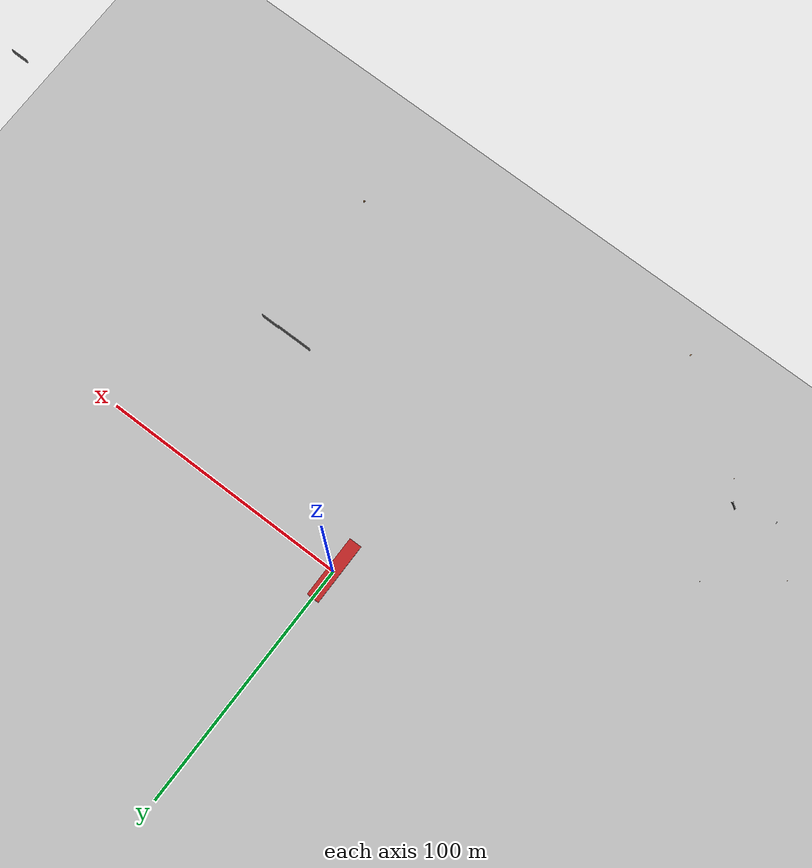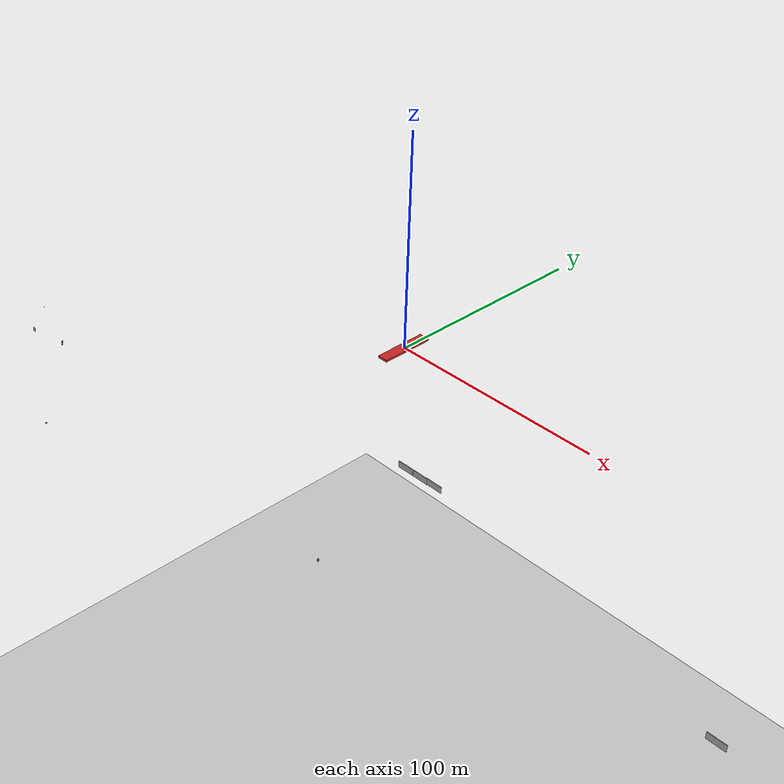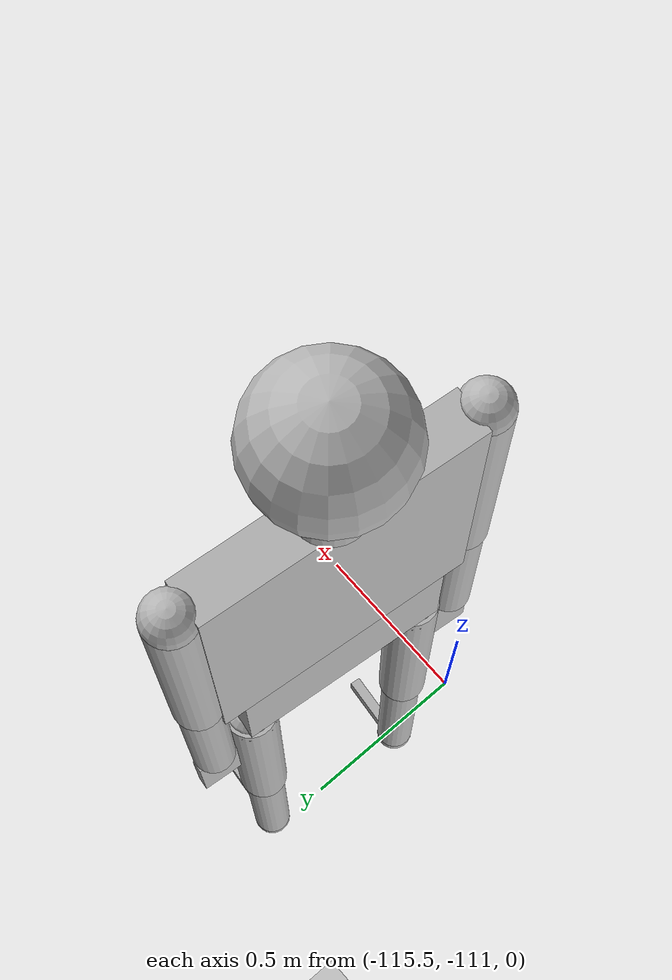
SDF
<sdf version="1.6">
 <world name="default">
  <light name="sun" type="directional">
   <pose>0 0 10 0 -0 0</pose>
   <diffuse>0.8 0.8 0.8 1</diffuse>
   <specular>0.2 0.2 0.2 1</specular>
   <attenuation>
    <range>1000</range>
    <constant>0.9</constant>
    <linear>0.01</linear>
    <quadratic>0.001</quadratic>
   </attenuation>
   <direction>-0.5 0.1 -0.9</direction>
  </light>
  <model name="ground_plane">
   <pose>0 0 -333 0 -0 0</pose>
   <static>1</static>
   <link name="link">
    <collision name="collision">
     <geometry><plane><normal>0 0 1</normal><size>100 100</size></plane></geometry>
     <surface><friction><ode><mu>100</mu><mu2>50</mu2></ode></friction></surface>
    </collision>
    <visual name="visual">
     <cast_shadows>0</cast_shadows>
     <geometry><plane><normal>0 0 1</normal><size>100 100</size></plane></geometry>
     <material>
      <script><uri>file://media/materials/scripts/gazebo.material</uri><name>Gazebo/Grey</name></script>
     </material>
    </visual>
    <enable_wind>1</enable_wind>
   </link>
   <enable_wind>1</enable_wind>
  </model>
  <gravity>0 0 -9.8</gravity>
  <magnetic_field>6e-06 2.3e-05 -4.2e-05</magnetic_field>
  <atmosphere type="adiabatic"/>
  <physics name="default_physics" default="0" type="ode">
   <max_step_size>0.001</max_step_size>
   <real_time_factor>1</real_time_factor>
   <real_time_update_rate>1000</real_time_update_rate>
  </physics>
  <scene><ambient>0.4 0.4 0.4 1</ambient><background>0.7 0.7 0.7 1</background><shadows>1</shadows></scene>
  <audio><device>default</device></audio>
  <spherical_coordinates>
   <surface_model>EARTH_WGS84</surface_model>
   <latitude_deg>0</latitude_deg>
   <longitude_deg>0</longitude_deg>
   <elevation>0</elevation>
   <heading_deg>0</heading_deg>
  </spherical_coordinates>
  <model name="robot_description">
   <link name="base_link">
    <inertial>
     <pose>0 0 5e-06 0 -0 0</pose>
     <mass>125</mass>
     <inertia><ixx>6520.01</ixx><ixy>0</ixy><ixz>0</ixz><iyy>6770</iyy><iyz>0</iyz><izz>270.007</izz></inertia>
    </inertial>
    <collision name="base_link_collision"><geometry><box><size>5.1 25.1 0.1</size></box></geometry></collision>
    <collision name="base_link_fixed_joint_lump__camera_link_1_collision_1">
     <pose>0 12.5 7 0 -0 2.01</pose>
     <geometry><box><size>0.08 0.04 0.04</size></box></geometry>
    </collision>
    <collision name="base_link_fixed_joint_lump__camera_link_2_collision_2">
     <pose>0 12.5 7 0 -0 1.13</pose>
     <geometry><box><size>0.08 0.04 0.04</size></box></geometry>
    </collision>
    <collision name="base_link_fixed_joint_lump__camera_link_3_collision_3">
     <pose>0 -12.5 7 0 0 -1.13</pose>
     <geometry><box><size>0.08 0.04 0.04</size></box></geometry>
    </collision>
    <collision name="base_link_fixed_joint_lump__camera_link_4_collision_4">
     <pose>0 -12.5 7 0 0 -2.01</pose>
     <geometry><box><size>0.08 0.04 0.04</size></box></geometry>
    </collision>
    <collision name="base_link_fixed_joint_lump__camera_link_5_collision_5">
     <pose>2.5 0 8 0 -0 0.44</pose>
     <geometry><box><size>0.08 0.04 0.04</size></box></geometry>
    </collision>
    <collision name="base_link_fixed_joint_lump__camera_link_6_collision_6">
     <pose>2.5 0 8 0 0 -0.44</pose>
     <geometry><box><size>0.08 0.04 0.04</size></box></geometry>
    </collision>
    <collision name="base_link_fixed_joint_lump__camera_link_7_collision_7">
     <pose>-2.5 0 8 0 -0 -2.70319</pose>
     <geometry><box><size>0.08 0.04 0.04</size></box></geometry>
    </collision>
    <collision name="base_link_fixed_joint_lump__camera_link_8_collision_8">
     <pose>-2.5 0 8 0 -0 2.7</pose>
     <geometry><box><size>0.08 0.04 0.04</size></box></geometry>
    </collision>
    <visual name="base_link_visual">
     <geometry><box><size>5 25 1</size></box></geometry>
     <material>
      <script><name>Gazebo/Red</name><uri>file://media/materials/scripts/gazebo.material</uri></script>
     </material>
    </visual>
    <visual name="base_link_fixed_joint_lump__camera_link_1_visual_1">
     <pose>0 12.5 7 0 -0 2.01</pose>
     <geometry><box><size>0.08 0.04 0.04</size></box></geometry>
     <material><script><uri>__default__</uri><name>__default__</name></script></material>
    </visual>
    <visual name="base_link_fixed_joint_lump__camera_link_2_visual_2">
     <pose>0 12.5 7 0 -0 1.13</pose>
     <geometry><box><size>0.08 0.04 0.04</size></box></geometry>
     <material><script><uri>__default__</uri><name>__default__</name></script></material>
    </visual>
    <visual name="base_link_fixed_joint_lump__camera_link_3_visual_3">
     <pose>0 -12.5 7 0 0 -1.13</pose>
     <geometry><box><size>0.08 0.04 0.04</size></box></geometry>
     <material><script><uri>__default__</uri><name>__default__</name></script></material>
    </visual>
    <visual name="base_link_fixed_joint_lump__camera_link_4_visual_4">
     <pose>0 -12.5 7 0 0 -2.01</pose>
     <geometry><box><size>0.08 0.04 0.04</size></box></geometry>
     <material><script><uri>__default__</uri><name>__default__</name></script></material>
    </visual>
    <visual name="base_link_fixed_joint_lump__camera_link_5_visual_5">
     <pose>2.5 0 8 0 -0 0.44</pose>
     <geometry><box><size>0.08 0.04 0.04</size></box></geometry>
     <material><script><uri>__default__</uri><name>__default__</name></script></material>
    </visual>
    <visual name="base_link_fixed_joint_lump__camera_link_6_visual_6">
     <pose>2.5 0 8 0 0 -0.44</pose>
     <geometry><box><size>0.08 0.04 0.04</size></box></geometry>
     <material><script><uri>__default__</uri><name>__default__</name></script></material>
    </visual>
    <visual name="base_link_fixed_joint_lump__camera_link_7_visual_7">
     <pose>-2.5 0 8 0 -0 -2.70319</pose>
     <geometry><box><size>0.08 0.04 0.04</size></box></geometry>
     <material><script><uri>__default__</uri><name>__default__</name></script></material>
    </visual>
    <visual name="base_link_fixed_joint_lump__camera_link_8_visual_8">
     <pose>-2.5 0 8 0 -0 2.7</pose>
     <geometry><box><size>0.08 0.04 0.04</size></box></geometry>
     <material><script><uri>__default__</uri><name>__default__</name></script></material>
    </visual>
    <sensor name="camera_1" type="camera">
     <update_rate>20</update_rate>
     <camera name="head">
      <horizontal_fov>1.22</horizontal_fov>
      <image><width>1920</width><height>1080</height><format>R8G8B8</format></image>
      <clip><near>0.02</near><far>300</far></clip>
      <noise><type>gaussian</type><mean>0</mean><stddev>0.007</stddev></noise>
     </camera>
     <plugin name="camera_controller" filename="libgazebo_ros_camera.so">
      <alwaysOn>1</alwaysOn>
      <updateRate>0.0</updateRate>
      <cameraName>camera_1</cameraName>
      <imageTopicName>camera_1_raw</imageTopicName>
      <cameraInfoTopicName>camera_1_info</cameraInfoTopicName>
      <frameName>camera_link_1</frameName>
      <hackBaseline>0.07</hackBaseline>
      <distortionK1>0.0</distortionK1>
      <distortionK2>0.0</distortionK2>
      <distortionK3>0.0</distortionK3>
      <distortionT1>0.0</distortionT1>
      <distortionT2>0.0</distortionT2>
      <robotNamespace>/</robotNamespace>
     </plugin>
     <pose>0 12.5 7 0 -0 2.01</pose>
    </sensor>
    <sensor name="camera_2" type="camera">
     <update_rate>20</update_rate>
     <camera name="head">
      <horizontal_fov>1.22</horizontal_fov>
      <image><width>1920</width><height>1080</height><format>R8G8B8</format></image>
      <clip><near>0.02</near><far>300</far></clip>
      <noise><type>gaussian</type><mean>0</mean><stddev>0.007</stddev></noise>
     </camera>
     <plugin name="camera_controller" filename="libgazebo_ros_camera.so">
      <alwaysOn>1</alwaysOn>
      <updateRate>0.0</updateRate>
      <cameraName>camera_2</cameraName>
      <imageTopicName>camera_2_raw</imageTopicName>
      <cameraInfoTopicName>camera_2_info</cameraInfoTopicName>
      <frameName>camera_link_2</frameName>
      <hackBaseline>0.07</hackBaseline>
      <distortionK1>0.0</distortionK1>
      <distortionK2>0.0</distortionK2>
      <distortionK3>0.0</distortionK3>
      <distortionT1>0.0</distortionT1>
      <distortionT2>0.0</distortionT2>
      <robotNamespace>/</robotNamespace>
     </plugin>
     <pose>0 12.5 7 0 -0 1.13</pose>
    </sensor>
    <sensor name="camera_3" type="camera">
     <update_rate>20</update_rate>
     <camera name="head">
      <horizontal_fov>1.22</horizontal_fov>
      <image><width>1920</width><height>1080</height><format>R8G8B8</format></image>
      <clip><near>0.02</near><far>300</far></clip>
      <noise><type>gaussian</type><mean>0</mean><stddev>0.007</stddev></noise>
     </camera>
     <plugin name="camera_controller" filename="libgazebo_ros_camera.so">
      <alwaysOn>1</alwaysOn>
      <updateRate>0.0</updateRate>
      <cameraName>camera_3</cameraName>
      <imageTopicName>camera_3_raw</imageTopicName>
      <cameraInfoTopicName>camera_3_info</cameraInfoTopicName>
      <frameName>camera_link_3</frameName>
      <hackBaseline>0.07</hackBaseline>
      <distortionK1>0.0</distortionK1>
      <distortionK2>0.0</distortionK2>
      <distortionK3>0.0</distortionK3>
      <distortionT1>0.0</distortionT1>
      <distortionT2>0.0</distortionT2>
      <robotNamespace>/</robotNamespace>
     </plugin>
     <pose>0 -12.5 7 0 0 -1.13</pose>
    </sensor>
    <sensor name="camera_4" type="camera">
     <update_rate>20</update_rate>
     <camera name="head">
      <horizontal_fov>1.22</horizontal_fov>
      <image><width>1920</width><height>1080</height><format>R8G8B8</format></image>
      <clip><near>0.02</near><far>300</far></clip>
      <noise><type>gaussian</type><mean>0</mean><stddev>0.007</stddev></noise>
     </camera>
     <plugin name="camera_controller" filename="libgazebo_ros_camera.so">
      <alwaysOn>1</alwaysOn>
      <updateRate>0.0</updateRate>
      <cameraName>camera_4</cameraName>
      <imageTopicName>camera_4_raw</imageTopicName>
      <cameraInfoTopicName>camera_4_info</cameraInfoTopicName>
      <frameName>camera_link_4</frameName>
      <hackBaseline>0.07</hackBaseline>
      <distortionK1>0.0</distortionK1>
      <distortionK2>0.0</distortionK2>
      <distortionK3>0.0</distortionK3>
      <distortionT1>0.0</distortionT1>
      <distortionT2>0.0</distortionT2>
      <robotNamespace>/</robotNamespace>
     </plugin>
     <pose>0 -12.5 7 0 0 -2.01</pose>
    </sensor>
    <sensor name="camera_5" type="camera">
     <update_rate>20</update_rate>
     <camera name="head">
      <horizontal_fov>1.22</horizontal_fov>
      <image><width>1920</width><height>1080</height><format>R8G8B8</format></image>
      <clip><near>0.02</near><far>300</far></clip>
      <noise><type>gaussian</type><mean>0</mean><stddev>0.007</stddev></noise>
     </camera>
     <plugin name="camera_controller" filename="libgazebo_ros_camera.so">
      <alwaysOn>1</alwaysOn>
      <updateRate>0.0</updateRate>
      <cameraName>camera_5</cameraName>
      <imageTopicName>camera_5_raw</imageTopicName>
      <cameraInfoTopicName>camera_5_info</cameraInfoTopicName>
      <frameName>camera_link_5</frameName>
      <hackBaseline>0.07</hackBaseline>
      <distortionK1>0.0</distortionK1>
      <distortionK2>0.0</distortionK2>
      <distortionK3>0.0</distortionK3>
      <distortionT1>0.0</distortionT1>
      <distortionT2>0.0</distortionT2>
      <robotNamespace>/</robotNamespace>
     </plugin>
     <pose>2.5 0 8 0 -0 0.44</pose>
    </sensor>
    <sensor name="camera_6" type="camera">
     <update_rate>20</update_rate>
     <camera name="head">
      <horizontal_fov>1.22</horizontal_fov>
      <image><width>1920</width><height>1080</height><format>R8G8B8</format></image>
      <clip><near>0.02</near><far>300</far></clip>
      <noise><type>gaussian</type><mean>0</mean><stddev>0.007</stddev></noise>
     </camera>
     <plugin name="camera_controller" filename="libgazebo_ros_camera.so">
      <alwaysOn>1</alwaysOn>
      <updateRate>0.0</updateRate>
      <cameraName>camera_6</cameraName>
      <imageTopicName>camera_6_raw</imageTopicName>
      <cameraInfoTopicName>camera_6_info</cameraInfoTopicName>
      <frameName>camera_link_6</frameName>
      <hackBaseline>0.07</hackBaseline>
      <distortionK1>0.0</distortionK1>
      <distortionK2>0.0</distortionK2>
      <distortionK3>0.0</distortionK3>
      <distortionT1>0.0</distortionT1>
      <distortionT2>0.0</distortionT2>
      <robotNamespace>/</robotNamespace>
     </plugin>
     <pose>2.5 0 8 0 0 -0.44</pose>
    </sensor>
    <sensor name="camera_7" type="camera">
     <update_rate>20</update_rate>
     <camera name="head">
      <horizontal_fov>1.22</horizontal_fov>
      <image><width>1920</width><height>1080</height><format>R8G8B8</format></image>
      <clip><near>0.02</near><far>300</far></clip>
      <noise><type>gaussian</type><mean>0</mean><stddev>0.007</stddev></noise>
     </camera>
     <plugin name="camera_controller" filename="libgazebo_ros_camera.so">
      <alwaysOn>1</alwaysOn>
      <updateRate>0.0</updateRate>
      <cameraName>camera_7</cameraName>
      <imageTopicName>camera_7_raw</imageTopicName>
      <cameraInfoTopicName>camera_7_info</cameraInfoTopicName>
      <frameName>camera_link_7</frameName>
      <hackBaseline>0.07</hackBaseline>
      <distortionK1>0.0</distortionK1>
      <distortionK2>0.0</distortionK2>
      <distortionK3>0.0</distortionK3>
      <distortionT1>0.0</distortionT1>
      <distortionT2>0.0</distortionT2>
      <robotNamespace>/</robotNamespace>
     </plugin>
     <pose>-2.5 0 8 0 -0 -2.70319</pose>
    </sensor>
    <sensor name="camera_8" type="camera">
     <update_rate>20</update_rate>
     <camera name="head">
      <horizontal_fov>1.22</horizontal_fov>
      <image><width>1920</width><height>1080</height><format>R8G8B8</format></image>
      <clip><near>0.02</near><far>300</far></clip>
      <noise><type>gaussian</type><mean>0</mean><stddev>0.007</stddev></noise>
     </camera>
     <plugin name="camera_controller" filename="libgazebo_ros_camera.so">
      <alwaysOn>1</alwaysOn>
      <updateRate>0.0</updateRate>
      <cameraName>camera_8</cameraName>
      <imageTopicName>camera_8_raw</imageTopicName>
      <cameraInfoTopicName>camera_8_info</cameraInfoTopicName>
      <frameName>camera_link_8</frameName>
      <hackBaseline>0.07</hackBaseline>
      <distortionK1>0.0</distortionK1>
      <distortionK2>0.0</distortionK2>
      <distortionK3>0.0</distortionK3>
      <distortionT1>0.0</distortionT1>
      <distortionT2>0.0</distortionT2>
      <robotNamespace>/</robotNamespace>
     </plugin>
     <pose>-2.5 0 8 0 -0 2.7</pose>
    </sensor>
   </link>
   <static>0</static>
   <plugin name="ground_truth_odometry" filename="libgazebo_ros_p3d.so">
    <alwaysOn>1</alwaysOn>
    <updateRate>100.0</updateRate>
    <bodyName>base_link</bodyName>
    <topicName>base_pose_ground_truth</topicName>
    <gaussianNoise>0.5</gaussianNoise>
    <frameName>map</frameName>
    <xyzOffsets>0 0 0</xyzOffsets>
    <rpyOffsets>0 0 0</rpyOffsets>
    <robotNamespace>/</robotNamespace>
   </plugin>
   <pose>-0.156275 -0.725161 0.05 0 -0 0.003976</pose>
  </model>
  <model name="cabinet">
   <static>1</static>
   <link name="cabinet_bottom_plate">
    <inertial>
     <pose>0 0 -1 0 -0 0</pose>
     <inertia><ixx>2.05</ixx><ixy>0</ixy><ixz>0</ixz><iyy>2.05</iyy><iyz>0</iyz><izz>2.05</izz></inertia>
     <mass>25</mass>
    </inertial>
    <collision name="cabinet_bottom_plate_geom">
     <pose>0 0 0.01 0 -0 0</pose>
     <geometry><box><size>0.45 0.45 0.02</size></box></geometry>
    </collision>
    <visual name="cabinet_bottom_plate_geom_visual">
     <pose>0 0 0.01 0 -0 0</pose>
     <geometry><box><size>0.45 0.45 0.02</size></box></geometry>
     <material>
      <script><uri>file://media/materials/scripts/gazebo.material</uri><name>Gazebo/Wood</name></script>
     </material>
    </visual>
    <collision name="cabinet_bottom_plate_geom_cabinet_back_plate">
     <pose>0.235 0 0.51 0 -0 0</pose>
     <geometry><box><size>0.02 0.45 1.02</size></box></geometry>
    </collision>
    <visual name="cabinet_bottom_plate_geom_cabinet_back_plate_visual">
     <pose>0.235 0 0.51 0 -0 0</pose>
     <geometry><box><size>0.02 0.45 1.02</size></box></geometry>
     <material>
      <script><uri>file://media/materials/scripts/gazebo.material</uri><name>Gazebo/Wood</name></script>
     </material>
    </visual>
    <collision name="cabinet_bottom_plate_geom_cabinet_left_plate">
     <pose>0 0.235 0.51 0 -0 0</pose>
     <geometry><box><size>0.45 0.02 1.02</size></box></geometry>
    </collision>
    <visual name="cabinet_bottom_plate_geom_cabinet_left_plate_visual">
     <pose>0 0.235 0.51 0 -0 0</pose>
     <geometry><box><size>0.45 0.02 1.02</size></box></geometry>
     <material>
      <script><uri>file://media/materials/scripts/gazebo.material</uri><name>Gazebo/Wood</name></script>
     </material>
    </visual>
    <collision name="cabinet_bottom_plate_geom_cabinet_middle_plate">
     <pose>0 0 0.51 0 -0 0</pose>
     <geometry><box><size>0.45 0.45 0.02</size></box></geometry>
    </collision>
    <visual name="cabinet_bottom_plate_geom_cabinet_middle_plate_visual">
     <pose>0 0 0.51 0 -0 0</pose>
     <geometry><box><size>0.45 0.45 0.02</size></box></geometry>
     <material>
      <script><uri>file://media/materials/scripts/gazebo.material</uri><name>Gazebo/Wood</name></script>
     </material>
    </visual>
    <collision name="cabinet_bottom_plate_geom_cabinet_right_plate">
     <pose>0 -0.235 0.51 0 -0 0</pose>
     <geometry><box><size>0.45 0.02 1.02</size></box></geometry>
    </collision>
    <visual name="cabinet_bottom_plate_geom_cabinet_right_plate_visual">
     <pose>0 -0.235 0.51 0 -0 0</pose>
     <geometry><box><size>0.45 0.02 1.02</size></box></geometry>
     <material>
      <script><uri>file://media/materials/scripts/gazebo.material</uri><name>Gazebo/Wood</name></script>
     </material>
    </visual>
    <collision name="cabinet_bottom_plate_geom_cabinet_top_plate">
     <pose>0 0 1.01 0 -0 0</pose>
     <geometry><box><size>0.45 0.45 0.02</size></box></geometry>
    </collision>
    <visual name="cabinet_bottom_plate_geom_cabinet_top_plate_visual">
     <pose>0 0 1.01 0 -0 0</pose>
     <geometry><box><size>0.45 0.45 0.02</size></box></geometry>
     <material>
      <script><uri>file://media/materials/scripts/gazebo.material</uri><name>Gazebo/Wood</name></script>
     </material>
    </visual>
   </link>
   <pose>76.559 -117.77 0 0 -0 0</pose>
  </model>
  <model name="grey_wall">
   <static>1</static>
   <link name="link">
    <pose>0 0 1.4 0 -0 0</pose>
    <collision name="collision"><geometry><box><size>7.5 0.2 2.8</size></box></geometry></collision>
    <visual name="visual">
     <cast_shadows>0</cast_shadows>
     <geometry><box><size>7.5 0.2 2.8</size></box></geometry>
     <material>
      <script>
       <uri>model://grey_wall/materials/scripts</uri>
       <uri>model://grey_wall/materials/textures</uri>
       <name>vrc/grey_wall</name>
      </script>
     </material>
    </visual>
   </link>
   <pose>60.7126 -59.4919 0 0 -0 0</pose>
  </model>
  <model name="grey_wall_0">
   <static>1</static>
   <link name="link">
    <pose>0 0 1.4 0 -0 0</pose>
    <collision name="collision"><geometry><box><size>7.5 0.2 2.8</size></box></geometry></collision>
    <visual name="visual">
     <cast_shadows>0</cast_shadows>
     <geometry><box><size>7.5 0.2 2.8</size></box></geometry>
     <material>
      <script>
       <uri>model://grey_wall/materials/scripts</uri>
       <uri>model://grey_wall/materials/textures</uri>
       <name>vrc/grey_wall</name>
      </script>
     </material>
    </visual>
   </link>
   <pose>67.9501 -59.4577 0 0 -0 0</pose>
  </model>
  <model name="grey_wall_1">
   <static>1</static>
   <link name="link">
    <pose>0 0 1.4 0 -0 0</pose>
    <collision name="collision"><geometry><box><size>7.5 0.2 2.8</size></box></geometry></collision>
    <visual name="visual">
     <cast_shadows>0</cast_shadows>
     <geometry><box><size>7.5 0.2 2.8</size></box></geometry>
     <material>
      <script>
       <uri>model://grey_wall/materials/scripts</uri>
       <uri>model://grey_wall/materials/textures</uri>
       <name>vrc/grey_wall</name>
      </script>
     </material>
    </visual>
   </link>
   <pose>75.216 -59.2645 0 0 -0 0</pose>
  </model>
  <model name="wood_cube_10cm">
   <link name="link">
    <pose>0 0 0.05 0 -0 0</pose>
    <inertial>
     <mass>0.5167</mass>
     <inertia>
      <ixx>0.000861167</ixx>
      <ixy>0</ixy>
      <ixz>0</ixz>
      <iyy>0.000861167</iyy>
      <iyz>0</iyz>
      <izz>0.000861167</izz>
     </inertia>
    </inertial>
    <collision name="collision">
     <geometry><box><size>0.1 0.1 0.1</size></box></geometry>
     <surface>
      <contact>
       <poissons_ratio>0.347</poissons_ratio>
       <elastic_modulus>8.8e+09</elastic_modulus>
       <ode><kp>100000</kp><kd>100</kd><max_vel>100</max_vel><min_depth>0.001</min_depth></ode>
      </contact>
      <friction>
       <torsional>
        <coefficient>1</coefficient>
        <use_patch_radius>0</use_patch_radius>
        <surface_radius>0.01</surface_radius>
       </torsional>
      </friction>
     </surface>
    </collision>
    <visual name="visual">
     <geometry><box><size>0.1 0.1 0.1</size></box></geometry>
     <material>
      <script><uri>file://media/materials/scripts/gazebo.material</uri><name>Gazebo/Wood</name></script>
     </material>
    </visual>
   </link>
   <pose>-130.521 -96.0475 -0.001013 0 -0 0</pose>
  </model>
  <model name="wooden_board">
   <link name="base">
    <pose>0 0 0.00523 0 -0 0</pose>
    <inertial>
     <mass>0.2765</mass>
     <inertia>
      <ixx>0.0025148</ixx>
      <ixy>0</ixy>
      <ixz>0</ixz>
      <iyy>0.00024037</iyy>
      <iyz>0</iyz>
      <izz>0.00275013</izz>
     </inertia>
    </inertial>
    <collision name="collision">
     <geometry><box><size>0.1016 0.3302 0.01046</size></box></geometry>
     <surface>
      <contact>
       <poissons_ratio>0.347</poissons_ratio>
       <elastic_modulus>8.8e+09</elastic_modulus>
       <ode><kp>100000</kp><kd>100</kd><max_vel>100</max_vel><min_depth>0.001</min_depth></ode>
      </contact>
      <friction>
       <torsional>
        <coefficient>1</coefficient>
        <use_patch_radius>0</use_patch_radius>
        <surface_radius>0.01</surface_radius>
       </torsional>
      </friction>
     </surface>
    </collision>
    <visual name="visual">
     <geometry><box><size>0.1016 0.3302 0.01046</size></box></geometry>
     <material>
      <script><uri>file://media/materials/scripts/gazebo.material</uri><name>Gazebo/Wood</name></script>
     </material>
    </visual>
    <visual name="tee_nut_1">
     <pose>0 -0.116 0 0 -0 0</pose>
     <geometry><cylinder><radius>0.00635</radius><length>0.0105646</length></cylinder></geometry>
     <material>
      <script><uri>file://media/materials/scripts/gazebo.material</uri><name>Gazebo/Grey</name></script>
     </material>
    </visual>
    <visual name="tee_nut_2">
     <pose>0 -0.038 0 0 -0 0</pose>
     <geometry><cylinder><radius>0.00635</radius><length>0.0105646</length></cylinder></geometry>
     <material>
      <script><uri>file://media/materials/scripts/gazebo.material</uri><name>Gazebo/Grey</name></script>
     </material>
    </visual>
    <visual name="tee_nut_3">
     <pose>0 0.038 0 0 -0 0</pose>
     <geometry><cylinder><radius>0.00635</radius><length>0.0105646</length></cylinder></geometry>
     <material>
      <script><uri>file://media/materials/scripts/gazebo.material</uri><name>Gazebo/Grey</name></script>
     </material>
    </visual>
    <visual name="tee_nut_4">
     <pose>0 0.116 0 0 -0 0</pose>
     <geometry><cylinder><radius>0.00635</radius><length>0.0105646</length></cylinder></geometry>
     <material>
      <script><uri>file://media/materials/scripts/gazebo.material</uri><name>Gazebo/Grey</name></script>
     </material>
    </visual>
   </link>
   <pose>-105.929 -77.0336 -0.001007 0 -0 0</pose>
  </model>
  <model name="wooden_peg_board">
   <link name="wooden_board::base">
    <pose>0 0 0.00523 0 -0 0</pose>
    <inertial>
     <mass>0.2765</mass>
     <inertia>
      <ixx>0.0025148</ixx>
      <ixy>0</ixy>
      <ixz>0</ixz>
      <iyy>0.00024037</iyy>
      <iyz>0</iyz>
      <izz>0.00275013</izz>
     </inertia>
    </inertial>
    <collision name="collision">
     <geometry><box><size>0.1016 0.3302 0.01046</size></box></geometry>
     <surface>
      <contact>
       <poissons_ratio>0.347</poissons_ratio>
       <elastic_modulus>8.8e+09</elastic_modulus>
       <ode><kp>100000</kp><kd>100</kd><max_vel>100</max_vel><min_depth>0.001</min_depth></ode>
      </contact>
      <friction>
       <torsional>
        <coefficient>1</coefficient>
        <use_patch_radius>0</use_patch_radius>
        <surface_radius>0.01</surface_radius>
       </torsional>
      </friction>
     </surface>
    </collision>
    <visual name="visual">
     <geometry><box><size>0.1016 0.3302 0.01046</size></box></geometry>
     <material>
      <script><uri>file://media/materials/scripts/gazebo.material</uri><name>Gazebo/Wood</name></script>
     </material>
    </visual>
    <visual name="tee_nut_1">
     <pose>0 -0.116 0 0 -0 0</pose>
     <geometry><cylinder><radius>0.00635</radius><length>0.0105646</length></cylinder></geometry>
     <material>
      <script><uri>file://media/materials/scripts/gazebo.material</uri><name>Gazebo/Grey</name></script>
     </material>
    </visual>
    <visual name="tee_nut_2">
     <pose>0 -0.038 0 0 -0 0</pose>
     <geometry><cylinder><radius>0.00635</radius><length>0.0105646</length></cylinder></geometry>
     <material>
      <script><uri>file://media/materials/scripts/gazebo.material</uri><name>Gazebo/Grey</name></script>
     </material>
    </visual>
    <visual name="tee_nut_3">
     <pose>0 0.038 0 0 -0 0</pose>
     <geometry><cylinder><radius>0.00635</radius><length>0.0105646</length></cylinder></geometry>
     <material>
      <script><uri>file://media/materials/scripts/gazebo.material</uri><name>Gazebo/Grey</name></script>
     </material>
    </visual>
    <visual name="tee_nut_4">
     <pose>0 0.116 0 0 -0 0</pose>
     <geometry><cylinder><radius>0.00635</radius><length>0.0105646</length></cylinder></geometry>
     <material>
      <script><uri>file://media/materials/scripts/gazebo.material</uri><name>Gazebo/Grey</name></script>
     </material>
    </visual>
   </link>
   <link name="peg::link">
    <pose>0 0.116 0.04 0 -0 0</pose>
    <inertial>
     <mass>0.0175</mass>
     <inertia>
      <ixx>9.74923e-06</ixx>
      <ixy>0</ixy>
      <ixz>0</ixz>
      <iyy>9.74923e-06</iyy>
      <iyz>0</iyz>
      <izz>8.31797e-07</izz>
     </inertia>
    </inertial>
    <collision name="collision">
     <geometry><cylinder><radius>0.00975</radius><length>0.08</length></cylinder></geometry>
     <surface>
      <contact>
       <poissons_ratio>0.347</poissons_ratio>
       <elastic_modulus>8.8e+09</elastic_modulus>
       <ode><kp>100000</kp><kd>100</kd><max_vel>100</max_vel><min_depth>0.001</min_depth></ode>
      </contact>
      <friction>
       <torsional>
        <coefficient>1</coefficient>
        <use_patch_radius>0</use_patch_radius>
        <surface_radius>0.01</surface_radius>
       </torsional>
      </friction>
     </surface>
    </collision>
    <visual name="visual">
     <geometry><cylinder><radius>0.00975</radius><length>0.08</length></cylinder></geometry>
     <material>
      <script><uri>file://media/materials/scripts/gazebo.material</uri><name>Gazebo/Wood</name></script>
     </material>
    </visual>
   </link>
   <joint name="board_peg" type="revolute">
    <parent>wooden_board::base</parent>
    <child>peg::link</child>
    <axis>
     <xyz>0 0 1</xyz>
     <limit><upper>0</upper><lower>0</lower></limit>
     <use_parent_model_frame>0</use_parent_model_frame>
     <dynamics><spring_reference>0</spring_reference><spring_stiffness>0</spring_stiffness></dynamics>
    </axis>
   </joint>
   <pose>-94.3708 -115.163 -0.001004 1.3e-05 -1e-06 -1e-06</pose>
  </model>
  <model name="wooden_case">
   <link name="base">
    <pose>0 0 0.024 0 -0 0</pose>
    <inertial>
     <pose>-0.022184 0 0.171592 0 -0 0</pose>
     <mass>3.96264</mass>
     <inertia>
      <ixx>0.213536</ixx>
      <ixy>0</ixy>
      <ixz>0.000779377</ixz>
      <iyy>0.0708943</iyy>
      <iyz>0</iyz>
      <izz>0.154604</izz>
     </inertia>
    </inertial>
    <collision name="collision_back">
     <pose>-0.053975 0 0.1778 0 -0 0</pose>
     <geometry><box><size>0.01905 0.5461 0.3175</size></box></geometry>
     <surface>
      <contact>
       <poissons_ratio>0.347</poissons_ratio>
       <elastic_modulus>8.8e+09</elastic_modulus>
       <ode><kp>100000</kp><kd>100</kd><max_vel>100</max_vel><min_depth>0.001</min_depth></ode>
      </contact>
      <friction>
       <torsional>
        <coefficient>1</coefficient>
        <use_patch_radius>0</use_patch_radius>
        <surface_radius>0.01</surface_radius>
       </torsional>
      </friction>
     </surface>
    </collision>
    <visual name="visual_back">
     <pose>-0.053975 0 0.1778 0 -0 0</pose>
     <geometry><box><size>0.01905 0.5461 0.3175</size></box></geometry>
     <material>
      <script><uri>file://media/materials/scripts/gazebo.material</uri><name>Gazebo/Wood</name></script>
     </material>
    </visual>
    <collision name="collision_bottom">
     <pose>0 0 0.009525 0 -0 0</pose>
     <geometry><box><size>0.127 0.5842 0.01905</size></box></geometry>
     <surface>
      <contact>
       <poissons_ratio>0.347</poissons_ratio>
       <elastic_modulus>8.8e+09</elastic_modulus>
       <ode><kp>100000</kp><kd>100</kd><max_vel>100</max_vel><min_depth>0.001</min_depth></ode>
      </contact>
      <friction>
       <torsional>
        <coefficient>1</coefficient>
        <use_patch_radius>0</use_patch_radius>
        <surface_radius>0.01</surface_radius>
       </torsional>
      </friction>
     </surface>
    </collision>
    <visual name="visual_bottom">
     <pose>0 0 0.009525 0 -0 0</pose>
     <geometry><box><size>0.127 0.5842 0.01905</size></box></geometry>
     <material>
      <script><uri>file://media/materials/scripts/gazebo.material</uri><name>Gazebo/Wood</name></script>
     </material>
    </visual>
    <collision name="collision_top">
     <pose>0 0 0.346075 0 -0 0</pose>
     <geometry><box><size>0.127 0.5842 0.01905</size></box></geometry>
     <surface>
      <contact>
       <poissons_ratio>0.347</poissons_ratio>
       <elastic_modulus>8.8e+09</elastic_modulus>
       <ode><kp>100000</kp><kd>100</kd><max_vel>100</max_vel><min_depth>0.001</min_depth></ode>
      </contact>
      <friction>
       <torsional>
        <coefficient>1</coefficient>
        <use_patch_radius>0</use_patch_radius>
        <surface_radius>0.01</surface_radius>
       </torsional>
      </friction>
     </surface>
    </collision>
    <visual name="visual_top">
     <pose>0 0 0.346075 0 -0 0</pose>
     <geometry><box><size>0.127 0.5842 0.01905</size></box></geometry>
     <material>
      <script><uri>file://media/materials/scripts/gazebo.material</uri><name>Gazebo/Wood</name></script>
     </material>
    </visual>
    <collision name="collision_left">
     <pose>0 -0.282575 0.1778 0 -0 0</pose>
     <geometry><box><size>0.127 0.01905 0.3175</size></box></geometry>
     <surface>
      <contact>
       <poissons_ratio>0.347</poissons_ratio>
       <elastic_modulus>8.8e+09</elastic_modulus>
       <ode><kp>100000</kp><kd>100</kd><max_vel>100</max_vel><min_depth>0.001</min_depth></ode>
      </contact>
      <friction>
       <torsional>
        <coefficient>1</coefficient>
        <use_patch_radius>0</use_patch_radius>
        <surface_radius>0.01</surface_radius>
       </torsional>
      </friction>
     </surface>
    </collision>
    <visual name="visual_left">
     <pose>0 -0.282575 0.1778 0 -0 0</pose>
     <geometry><box><size>0.127 0.01905 0.3175</size></box></geometry>
     <material>
      <script><uri>file://media/materials/scripts/gazebo.material</uri><name>Gazebo/Wood</name></script>
     </material>
    </visual>
    <collision name="collision_right">
     <pose>0 0.282575 0.1778 0 -0 0</pose>
     <geometry><box><size>0.127 0.01905 0.3175</size></box></geometry>
     <surface>
      <contact>
       <poissons_ratio>0.347</poissons_ratio>
       <elastic_modulus>8.8e+09</elastic_modulus>
       <ode><kp>100000</kp><kd>100</kd><max_vel>100</max_vel><min_depth>0.001</min_depth></ode>
      </contact>
      <friction>
       <torsional>
        <coefficient>1</coefficient>
        <use_patch_radius>0</use_patch_radius>
        <surface_radius>0.01</surface_radius>
       </torsional>
      </friction>
     </surface>
    </collision>
    <visual name="visual_right">
     <pose>0 0.282575 0.1778 0 -0 0</pose>
     <geometry><box><size>0.127 0.01905 0.3175</size></box></geometry>
     <material>
      <script><uri>file://media/materials/scripts/gazebo.material</uri><name>Gazebo/Wood</name></script>
     </material>
    </visual>
    <collision name="collision_block_left">
     <pose>0.0095 -0.2151 -0.012 0 -0 0</pose>
     <geometry><box><size>0.108 0.05 0.024</size></box></geometry>
     <surface>
      <contact>
       <poissons_ratio>0.347</poissons_ratio>
       <elastic_modulus>8.8e+09</elastic_modulus>
       <ode><kp>100000</kp><kd>100</kd><max_vel>100</max_vel><min_depth>0.001</min_depth></ode>
      </contact>
      <friction>
       <torsional>
        <coefficient>1</coefficient>
        <use_patch_radius>0</use_patch_radius>
        <surface_radius>0.01</surface_radius>
       </torsional>
      </friction>
     </surface>
    </collision>
    <visual name="visual_block_left">
     <pose>0.0095 -0.2151 -0.012 0 -0 0</pose>
     <geometry><box><size>0.108 0.05 0.024</size></box></geometry>
     <material>
      <script><uri>file://media/materials/scripts/gazebo.material</uri><name>Gazebo/Wood</name></script>
     </material>
    </visual>
    <collision name="collision_block_right">
     <pose>0.0095 0.2151 -0.012 0 -0 0</pose>
     <geometry><box><size>0.108 0.05 0.024</size></box></geometry>
     <surface>
      <contact>
       <poissons_ratio>0.347</poissons_ratio>
       <elastic_modulus>8.8e+09</elastic_modulus>
       <ode><kp>100000</kp><kd>100</kd><max_vel>100</max_vel><min_depth>0.001</min_depth></ode>
      </contact>
      <friction>
       <torsional>
        <coefficient>1</coefficient>
        <use_patch_radius>0</use_patch_radius>
        <surface_radius>0.01</surface_radius>
       </torsional>
      </friction>
     </surface>
    </collision>
    <visual name="visual_block_right">
     <pose>0.0095 0.2151 -0.012 0 -0 0</pose>
     <geometry><box><size>0.108 0.05 0.024</size></box></geometry>
     <material>
      <script><uri>file://media/materials/scripts/gazebo.material</uri><name>Gazebo/Wood</name></script>
     </material>
    </visual>
   </link>
   <link name="lid">
    <pose>0.243775 0 0.009525 0 -0 0</pose>
    <inertial>
     <mass>1.97874</mass>
     <inertia>
      <ixx>0.0563367</ixx>
      <ixy>0</ixy>
      <ixz>0</ixz>
      <iyy>0.020911</iyy>
      <iyz>0</iyz>
      <izz>0.0771281</izz>
     </inertia>
    </inertial>
    <collision name="collision">
     <geometry><box><size>0.3556 0.5842 0.01905</size></box></geometry>
     <surface>
      <contact>
       <poissons_ratio>0.347</poissons_ratio>
       <elastic_modulus>8.8e+09</elastic_modulus>
       <ode><kp>100000</kp><kd>100</kd><max_vel>100</max_vel><min_depth>0.001</min_depth></ode>
      </contact>
      <friction>
       <torsional>
        <coefficient>1</coefficient>
        <use_patch_radius>0</use_patch_radius>
        <surface_radius>0.01</surface_radius>
       </torsional>
      </friction>
     </surface>
    </collision>
    <visual name="visual">
     <geometry><box><size>0.3556 0.5842 0.01905</size></box></geometry>
     <material>
      <script><uri>file://media/materials/scripts/gazebo.material</uri><name>Gazebo/Wood</name></script>
     </material>
    </visual>
    <visual name="tee_nut_1">
     <pose>0.122 -0.216 0 0 -0 0</pose>
     <geometry><cylinder><radius>0.00635</radius><length>0.0192405</length></cylinder></geometry>
     <material>
      <script><uri>file://media/materials/scripts/gazebo.material</uri><name>Gazebo/Grey</name></script>
     </material>
    </visual>
    <visual name="tee_nut_2">
     <pose>0.122 -0.088 0 0 -0 0</pose>
     <geometry><cylinder><radius>0.00635</radius><length>0.0192405</length></cylinder></geometry>
     <material>
      <script><uri>file://media/materials/scripts/gazebo.material</uri><name>Gazebo/Grey</name></script>
     </material>
    </visual>
    <visual name="tee_nut_3">
     <pose>0.122 0.088 0 0 -0 0</pose>
     <geometry><cylinder><radius>0.00635</radius><length>0.0192405</length></cylinder></geometry>
     <material>
      <script><uri>file://media/materials/scripts/gazebo.material</uri><name>Gazebo/Grey</name></script>
     </material>
    </visual>
    <visual name="tee_nut_4">
     <pose>0.122 0.216 0 0 -0 0</pose>
     <geometry><cylinder><radius>0.00635</radius><length>0.0192405</length></cylinder></geometry>
     <material>
      <script><uri>file://media/materials/scripts/gazebo.material</uri><name>Gazebo/Grey</name></script>
     </material>
    </visual>
   </link>
   <joint name="lid_hinge" type="revolute">
    <pose>-0.1778 0 0.01905 0 -0 0</pose>
    <parent>base</parent>
    <child>lid</child>
    <axis>
     <xyz>0 1 0</xyz>
     <limit><upper>0.523599</upper><lower>-1.5708</lower></limit>
     <use_parent_model_frame>0</use_parent_model_frame>
     <dynamics><spring_reference>0</spring_reference><spring_stiffness>0</spring_stiffness></dynamics>
    </axis>
   </joint>
   <pose>-55.4821 -143.397 -0.001057 0 -0.000429 0</pose>
  </model>
  <model name="submarine_sinking">
   <pose>-99.0187 -107.19 0.449062 1.49844 -0.515454 1.01753</pose>
   <link name="body">
    <pose>0 0 -1.07935 0 -0 0</pose>
    <inertial>
     <mass>1102.7</mass>
     <inertia><ixx>645.998</ixx><ixy>0</ixy><ixz>0</ixz><iyy>645.998</iyy><iyz>0</iyz><izz>49.6215</izz></inertia>
    </inertial>
    <visual name="body_visual">
     <geometry><cylinder><radius>0.3</radius><length>2.6</length></cylinder></geometry>
     <material>
      <script><uri>file://media/materials/scripts/gazebo.material</uri><name>Gazebo/Black</name></script>
     </material>
    </visual>
    <collision name="body_collision">
     <geometry><cylinder><radius>0.3</radius><length>2.6</length></cylinder></geometry>
    </collision>
    <visual name="spacer_visual">
     <pose>0 0 1.37855 0 -0 0</pose>
     <geometry><cylinder><radius>0.0933402</radius><length>0.127211</length></cylinder></geometry>
     <material>
      <script><uri>file://media/materials/scripts/gazebo.material</uri><name>Gazebo/Black</name></script>
     </material>
    </visual>
   </link>
   <link name="propeller">
    <pose>0 0 0.3455 3.14159 -0 0</pose>
    <inertial>
     <mass>25.2312</mass>
     <inertia><ixx>0.531907</ixx><ixy>0</ixy><ixz>0</ixz><iyy>0.531907</iyy><iyz>0</iyz><izz>1.0513</izz></inertia>
    </inertial>
    <visual name="blade1_visual">
     <pose>0.34334 0 0 0.785398 -0 0</pose>
     <geometry><box><size>0.5 0.154178 0.05455</size></box></geometry>
     <material>
      <script><uri>file://media/materials/scripts/gazebo.material</uri><name>Gazebo/Black</name></script>
     </material>
    </visual>
    <collision name="blade1_collision">
     <pose>0.34334 0 0 0.785398 -0 0</pose>
     <geometry><box><size>0.5 0.154178 0.05455</size></box></geometry>
    </collision>
    <visual name="blade2_visual">
     <pose>0 0.34334 0 0.785398 0 1.5708</pose>
     <geometry><box><size>0.5 0.154178 0.05455</size></box></geometry>
     <material>
      <script><uri>file://media/materials/scripts/gazebo.material</uri><name>Gazebo/Black</name></script>
     </material>
    </visual>
    <collision name="blade2_collision">
     <pose>0 0.34334 0 0.785398 0 1.5708</pose>
     <geometry><box><size>0.5 0.154178 0.05455</size></box></geometry>
    </collision>
    <visual name="blade3_visual">
     <pose>-0.34334 -0 0 -0.785398 0 0</pose>
     <geometry><box><size>0.5 0.154178 0.05455</size></box></geometry>
     <material>
      <script><uri>file://media/materials/scripts/gazebo.material</uri><name>Gazebo/Black</name></script>
     </material>
    </visual>
    <collision name="blade3_collision">
     <pose>-0.34334 -0 0 -0.785398 0 0</pose>
     <geometry><box><size>0.5 0.154178 0.05455</size></box></geometry>
    </collision>
    <visual name="blade4_visual">
     <pose>-0 -0.34334 0 -0.785398 -0 1.5708</pose>
     <geometry><box><size>0.5 0.154178 0.05455</size></box></geometry>
     <material>
      <script><uri>file://media/materials/scripts/gazebo.material</uri><name>Gazebo/Black</name></script>
     </material>
    </visual>
    <collision name="blade4_collision">
     <pose>-0 -0.34334 0 -0.785398 -0 1.5708</pose>
     <geometry><box><size>0.5 0.154178 0.05455</size></box></geometry>
    </collision>
   </link>
   <joint name="spinning_joint" type="revolute">
    <parent>body</parent>
    <child>propeller</child>
    <axis>
     <xyz>0 0 1</xyz>
     <use_parent_model_frame>1</use_parent_model_frame>
     <limit><lower>-1e+12</lower><upper>1e+12</upper><effort>-1</effort><velocity>-1</velocity></limit>
     <dynamics><spring_reference>0</spring_reference><spring_stiffness>0</spring_stiffness></dynamics>
    </axis>
   </joint>
   <plugin name="buoyancy" filename="libBuoyancyPlugin.so"><fluid_density>999.1026</fluid_density></plugin>
  </model>
  <model name="ragdoll">
   <pose>-115.477 -110.553 1.39977 3e-06 0.015813 -0.102365</pose>
   <link name="hip">
    <inertial>
     <inertia><ixx>0.1</ixx><ixy>0</ixy><ixz>0</ixz><iyy>0.1</iyy><iyz>0</iyz><izz>0.1</izz></inertia>
     <mass>10</mass>
    </inertial>
    <collision name="hip_geom">
     <pose>0 0 0.125 0 -0 0</pose>
     <geometry><box><size>0.1 0.5 0.25</size></box></geometry>
     <surface>
      <friction><ode><mu>-1</mu><mu2>-1</mu2><fdir1>0 0 0</fdir1><slip1>0</slip1><slip2>0</slip2></ode></friction>
      <bounce><restitution_coefficient>0</restitution_coefficient><threshold>100000</threshold></bounce>
      <contact>
       <ode>
        <soft_cfm>0</soft_cfm>
        <soft_erp>0.2</soft_erp>
        <kp>1e+12</kp>
        <kd>1</kd>
        <max_vel>0</max_vel>
        <min_depth>0.001</min_depth>
       </ode>
      </contact>
     </surface>
    </collision>
    <visual name="hip_geom_visual">
     <pose>0 0 0.125 0 -0 0</pose>
     <geometry><box><size>0.1 0.5 0.25</size></box></geometry>
    </visual>
    <gravity>0</gravity>
   </link>
   <link name="l_thigh_pan">
    <pose>0 0.22 0 0 -0 0</pose>
    <inertial>
     <inertia><ixx>0.01</ixx><ixy>0</ixy><ixz>0</ixz><iyy>0.01</iyy><iyz>0</iyz><izz>0.01</izz></inertia>
     <mass>1</mass>
    </inertial>
    <collision name="l_thigh_pan_geom">
     <pose>0 0 -0.03 0 -0 0</pose>
     <geometry><sphere><radius>0.06</radius></sphere></geometry>
     <surface>
      <friction><ode><mu>-1</mu><mu2>-1</mu2><fdir1>0 0 0</fdir1><slip1>0</slip1><slip2>0</slip2></ode></friction>
      <bounce><restitution_coefficient>0</restitution_coefficient><threshold>100000</threshold></bounce>
      <contact>
       <ode>
        <soft_cfm>0</soft_cfm>
        <soft_erp>0.2</soft_erp>
        <kp>1e+12</kp>
        <kd>1</kd>
        <max_vel>0</max_vel>
        <min_depth>0.001</min_depth>
       </ode>
      </contact>
     </surface>
    </collision>
    <visual name="l_thigh_pan_geom_visual">
     <pose>0 0 -0.03 0 -0 0</pose>
     <geometry><sphere><radius>0.06</radius></sphere></geometry>
    </visual>
    <gravity>0</gravity>
   </link>
   <link name="l_thigh_lift">
    <pose>0 0.22 0 0 -0 0</pose>
    <inertial>
     <inertia><ixx>0.05</ixx><ixy>0</ixy><ixz>0</ixz><iyy>0.05</iyy><iyz>0</iyz><izz>0.05</izz></inertia>
     <mass>5</mass>
    </inertial>
    <collision name="l_thigh_lift_geom">
     <pose>0 0 -0.35 0 -0 0</pose>
     <geometry><cylinder><radius>0.06</radius><length>0.7</length></cylinder></geometry>
     <surface>
      <friction><ode><mu>-1</mu><mu2>-1</mu2><fdir1>0 0 0</fdir1><slip1>0</slip1><slip2>0</slip2></ode></friction>
      <bounce><restitution_coefficient>0</restitution_coefficient><threshold>100000</threshold></bounce>
      <contact>
       <ode>
        <soft_cfm>0</soft_cfm>
        <soft_erp>0.2</soft_erp>
        <kp>1e+12</kp>
        <kd>1</kd>
        <max_vel>0</max_vel>
        <min_depth>0.001</min_depth>
       </ode>
      </contact>
     </surface>
    </collision>
    <visual name="l_thigh_lift_geom_visual">
     <pose>0 0 -0.35 0 -0 0</pose>
     <geometry><cylinder><radius>0.06</radius><length>0.7</length></cylinder></geometry>
    </visual>
    <gravity>0</gravity>
   </link>
   <link name="l_calf">
    <pose>0 0.22 -0.7 0 -0 0</pose>
    <inertial>
     <inertia><ixx>0.02</ixx><ixy>0</ixy><ixz>0</ixz><iyy>0.02</iyy><iyz>0</iyz><izz>0.02</izz></inertia>
     <mass>2</mass>
    </inertial>
    <collision name="l_calf_geom">
     <pose>0 0 -0.3 0 -0 0</pose>
     <geometry><cylinder><radius>0.05</radius><length>0.6</length></cylinder></geometry>
     <surface>
      <friction><ode><mu>-1</mu><mu2>-1</mu2><fdir1>0 0 0</fdir1><slip1>0</slip1><slip2>0</slip2></ode></friction>
      <bounce><restitution_coefficient>0</restitution_coefficient><threshold>100000</threshold></bounce>
      <contact>
       <ode>
        <soft_cfm>0</soft_cfm>
        <soft_erp>0.2</soft_erp>
        <kp>1e+12</kp>
        <kd>1</kd>
        <max_vel>0</max_vel>
        <min_depth>0.001</min_depth>
       </ode>
      </contact>
     </surface>
    </collision>
    <visual name="l_calf_geom_visual">
     <pose>0 0 -0.3 0 -0 0</pose>
     <geometry><cylinder><radius>0.05</radius><length>0.6</length></cylinder></geometry>
    </visual>
    <gravity>0</gravity>
   </link>
   <link name="l_ankle">
    <pose>0 0.22 -1.325 0 -0 0</pose>
    <inertial>
     <inertia><ixx>0.01</ixx><ixy>0</ixy><ixz>0</ixz><iyy>0.01</iyy><iyz>0</iyz><izz>0.01</izz></inertia>
     <mass>1</mass>
    </inertial>
    <collision name="l_ankle_geom">
     <geometry><sphere><radius>0.05</radius></sphere></geometry>
     <surface>
      <friction><ode><mu>-1</mu><mu2>-1</mu2><fdir1>0 0 0</fdir1><slip1>0</slip1><slip2>0</slip2></ode></friction>
      <bounce><restitution_coefficient>0</restitution_coefficient><threshold>100000</threshold></bounce>
      <contact>
       <ode>
        <soft_cfm>0</soft_cfm>
        <soft_erp>0.2</soft_erp>
        <kp>1e+12</kp>
        <kd>1</kd>
        <max_vel>0</max_vel>
        <min_depth>0.001</min_depth>
       </ode>
      </contact>
     </surface>
    </collision>
    <visual name="l_ankle_geom_visual"><geometry><sphere><radius>0.05</radius></sphere></geometry></visual>
    <gravity>0</gravity>
   </link>
   <link name="l_foot">
    <pose>0 0.22 -1.35 0 -0 0</pose>
    <inertial>
     <pose>0.1 0 0 0 -0 0</pose>
     <inertia><ixx>0.01</ixx><ixy>0</ixy><ixz>0</ixz><iyy>0.01</iyy><iyz>0</iyz><izz>0.01</izz></inertia>
     <mass>1</mass>
    </inertial>
    <collision name="l_foot_geom">
     <pose>0.1 0 -0.025 0 -0 0</pose>
     <geometry><box><size>0.2 0.03 0.05</size></box></geometry>
     <surface>
      <friction><ode><mu>-1</mu><mu2>-1</mu2><fdir1>0 0 0</fdir1><slip1>0</slip1><slip2>0</slip2></ode></friction>
      <bounce><restitution_coefficient>0</restitution_coefficient><threshold>100000</threshold></bounce>
      <contact>
       <ode>
        <soft_cfm>0</soft_cfm>
        <soft_erp>0.2</soft_erp>
        <kp>1e+12</kp>
        <kd>1</kd>
        <max_vel>0</max_vel>
        <min_depth>0.001</min_depth>
       </ode>
      </contact>
     </surface>
    </collision>
    <visual name="l_foot_geom_visual">
     <pose>0.1 0 -0.025 0 -0 0</pose>
     <geometry><box><size>0.2 0.03 0.05</size></box></geometry>
    </visual>
   </link>
   <link name="r_thigh_pan">
    <pose>0 -0.22 0 0 -0 0</pose>
    <inertial>
     <inertia><ixx>0.01</ixx><ixy>0</ixy><ixz>0</ixz><iyy>0.01</iyy><iyz>0</iyz><izz>0.01</izz></inertia>
     <mass>1</mass>
    </inertial>
    <collision name="r_thigh_pan_geom">
     <pose>0 0 -0.03 0 -0 0</pose>
     <geometry><sphere><radius>0.06</radius></sphere></geometry>
     <surface>
      <friction><ode><mu>-1</mu><mu2>-1</mu2><fdir1>0 0 0</fdir1><slip1>0</slip1><slip2>0</slip2></ode></friction>
      <bounce><restitution_coefficient>0</restitution_coefficient><threshold>100000</threshold></bounce>
      <contact>
       <ode>
        <soft_cfm>0</soft_cfm>
        <soft_erp>0.2</soft_erp>
        <kp>1e+12</kp>
        <kd>1</kd>
        <max_vel>0</max_vel>
        <min_depth>0.001</min_depth>
       </ode>
      </contact>
     </surface>
    </collision>
    <visual name="r_thigh_pan_geom_visual">
     <pose>0 0 -0.03 0 -0 0</pose>
     <geometry><sphere><radius>0.06</radius></sphere></geometry>
    </visual>
    <gravity>0</gravity>
   </link>
   <link name="r_thigh_lift">
    <pose>0 -0.22 0 0 -0 0</pose>
    <inertial>
     <inertia><ixx>0.05</ixx><ixy>0</ixy><ixz>0</ixz><iyy>0.05</iyy><iyz>0</iyz><izz>0.05</izz></inertia>
     <mass>5</mass>
    </inertial>
    <collision name="r_thigh_lift_geom">
     <pose>0 0 -0.35 0 -0 0</pose>
     <geometry><cylinder><radius>0.06</radius><length>0.7</length></cylinder></geometry>
     <surface>
      <friction><ode><mu>-1</mu><mu2>-1</mu2><fdir1>0 0 0</fdir1><slip1>0</slip1><slip2>0</slip2></ode></friction>
      <bounce><restitution_coefficient>0</restitution_coefficient><threshold>100000</threshold></bounce>
      <contact>
       <ode>
        <soft_cfm>0</soft_cfm>
        <soft_erp>0.2</soft_erp>
        <kp>1e+12</kp>
        <kd>1</kd>
        <max_vel>0</max_vel>
        <min_depth>0.001</min_depth>
       </ode>
      </contact>
     </surface>
    </collision>
    <visual name="r_thigh_lift_geom_visual">
     <pose>0 0 -0.35 0 -0 0</pose>
     <geometry><cylinder><radius>0.06</radius><length>0.7</length></cylinder></geometry>
    </visual>
    <gravity>0</gravity>
   </link>
   <link name="r_calf">
    <pose>0 -0.22 -0.7 0 -0 0</pose>
    <inertial>
     <inertia><ixx>0.02</ixx><ixy>0</ixy><ixz>0</ixz><iyy>0.02</iyy><iyz>0</iyz><izz>0.02</izz></inertia>
     <mass>2</mass>
    </inertial>
    <collision name="r_calf_geom">
     <pose>0 0 -0.3 0 -0 0</pose>
     <geometry><cylinder><radius>0.05</radius><length>0.6</length></cylinder></geometry>
     <surface>
      <friction><ode><mu>-1</mu><mu2>-1</mu2><fdir1>0 0 0</fdir1><slip1>0</slip1><slip2>0</slip2></ode></friction>
      <bounce><restitution_coefficient>0</restitution_coefficient><threshold>100000</threshold></bounce>
      <contact>
       <ode>
        <soft_cfm>0</soft_cfm>
        <soft_erp>0.2</soft_erp>
        <kp>1e+12</kp>
        <kd>1</kd>
        <max_vel>0</max_vel>
        <min_depth>0.001</min_depth>
       </ode>
      </contact>
     </surface>
    </collision>
    <visual name="r_calf_geom_visual">
     <pose>0 0 -0.3 0 -0 0</pose>
     <geometry><cylinder><radius>0.05</radius><length>0.6</length></cylinder></geometry>
    </visual>
    <gravity>0</gravity>
   </link>
   <link name="r_ankle">
    <pose>0 -0.22 -1.325 0 -0 0</pose>
    <inertial>
     <inertia><ixx>0.01</ixx><ixy>0</ixy><ixz>0</ixz><iyy>0.01</iyy><iyz>0</iyz><izz>0.01</izz></inertia>
     <mass>1</mass>
    </inertial>
    <collision name="r_ankle_geom">
     <geometry><sphere><radius>0.05</radius></sphere></geometry>
     <surface>
      <friction><ode><mu>-1</mu><mu2>-1</mu2><fdir1>0 0 0</fdir1><slip1>0</slip1><slip2>0</slip2></ode></friction>
      <bounce><restitution_coefficient>0</restitution_coefficient><threshold>100000</threshold></bounce>
      <contact>
       <ode>
        <soft_cfm>0</soft_cfm>
        <soft_erp>0.2</soft_erp>
        <kp>1e+12</kp>
        <kd>1</kd>
        <max_vel>0</max_vel>
        <min_depth>0.001</min_depth>
       </ode>
      </contact>
     </surface>
    </collision>
    <visual name="r_ankle_geom_visual"><geometry><sphere><radius>0.05</radius></sphere></geometry></visual>
    <gravity>0</gravity>
   </link>
   <link name="r_foot">
    <pose>0 -0.22 -1.35 0 -0 0</pose>
    <inertial>
     <pose>0.1 0 0 0 -0 0</pose>
     <inertia><ixx>0.01</ixx><ixy>0</ixy><ixz>0</ixz><iyy>0.01</iyy><iyz>0</iyz><izz>0.01</izz></inertia>
     <mass>1</mass>
    </inertial>
    <collision name="r_foot_geom">
     <pose>0.1 0 -0.025 0 -0 0</pose>
     <geometry><box><size>0.2 0.03 0.05</size></box></geometry>
     <surface>
      <friction><ode><mu>-1</mu><mu2>-1</mu2><fdir1>0 0 0</fdir1><slip1>0</slip1><slip2>0</slip2></ode></friction>
      <bounce><restitution_coefficient>0</restitution_coefficient><threshold>100000</threshold></bounce>
      <contact>
       <ode>
        <soft_cfm>0</soft_cfm>
        <soft_erp>0.2</soft_erp>
        <kp>1e+12</kp>
        <kd>1</kd>
        <max_vel>0</max_vel>
        <min_depth>0.001</min_depth>
       </ode>
      </contact>
     </surface>
    </collision>
    <visual name="r_foot_geom_visual">
     <pose>0.1 0 -0.025 0 -0 0</pose>
     <geometry><box><size>0.2 0.03 0.05</size></box></geometry>
    </visual>
   </link>
   <link name="torso">
    <pose>0 0 0.25 0 -0 0</pose>
    <inertial>
     <inertia><ixx>0.3</ixx><ixy>0</ixy><ixz>0</ixz><iyy>0.3</iyy><iyz>0</iyz><izz>0.3</izz></inertia>
     <mass>30</mass>
    </inertial>
    <collision name="torso_geom">
     <pose>0 0 0.35 0 -0 0</pose>
     <geometry><box><size>0.1 0.6 0.7</size></box></geometry>
     <surface>
      <friction><ode><mu>-1</mu><mu2>-1</mu2><fdir1>0 0 0</fdir1><slip1>0</slip1><slip2>0</slip2></ode></friction>
      <bounce><restitution_coefficient>0</restitution_coefficient><threshold>100000</threshold></bounce>
      <contact>
       <ode>
        <soft_cfm>0</soft_cfm>
        <soft_erp>0.2</soft_erp>
        <kp>1e+12</kp>
        <kd>1</kd>
        <max_vel>0</max_vel>
        <min_depth>0.001</min_depth>
       </ode>
      </contact>
     </surface>
    </collision>
    <visual name="torso_geom_visual">
     <pose>0 0 0.35 0 -0 0</pose>
     <geometry><box><size>0.1 0.6 0.7</size></box></geometry>
    </visual>
    <gravity>0</gravity>
   </link>
   <link name="l_shoulder">
    <pose>0 0.3275 0.9225 0 -0 0</pose>
    <inertial>
     <inertia><ixx>0.01</ixx><ixy>0</ixy><ixz>0</ixz><iyy>0.01</iyy><iyz>0</iyz><izz>0.01</izz></inertia>
     <mass>1</mass>
    </inertial>
    <collision name="l_shoulder_geom">
     <geometry><sphere><radius>0.055</radius></sphere></geometry>
     <surface>
      <friction><ode><mu>-1</mu><mu2>-1</mu2><fdir1>0 0 0</fdir1><slip1>0</slip1><slip2>0</slip2></ode></friction>
      <bounce><restitution_coefficient>0</restitution_coefficient><threshold>100000</threshold></bounce>
      <contact>
       <ode>
        <soft_cfm>0</soft_cfm>
        <soft_erp>0.2</soft_erp>
        <kp>1e+12</kp>
        <kd>1</kd>
        <max_vel>0</max_vel>
        <min_depth>0.001</min_depth>
       </ode>
      </contact>
     </surface>
    </collision>
    <visual name="l_shoulder_geom_visual"><geometry><sphere><radius>0.055</radius></sphere></geometry></visual>
    <gravity>0</gravity>
   </link>
   <link name="l_upper_arm">
    <pose>0 0.3275 0.9225 0 -0 0</pose>
    <inertial>
     <inertia><ixx>0.02</ixx><ixy>0</ixy><ixz>0</ixz><iyy>0.02</iyy><iyz>0</iyz><izz>0.02</izz></inertia>
     <mass>2</mass>
    </inertial>
    <collision name="l_upper_arm_geom">
     <pose>0 0 -0.3 0 -0 0</pose>
     <geometry><cylinder><radius>0.055</radius><length>0.6</length></cylinder></geometry>
     <surface>
      <friction><ode><mu>-1</mu><mu2>-1</mu2><fdir1>0 0 0</fdir1><slip1>0</slip1><slip2>0</slip2></ode></friction>
      <bounce><restitution_coefficient>0</restitution_coefficient><threshold>100000</threshold></bounce>
      <contact>
       <ode>
        <soft_cfm>0</soft_cfm>
        <soft_erp>0.2</soft_erp>
        <kp>1e+12</kp>
        <kd>1</kd>
        <max_vel>0</max_vel>
        <min_depth>0.001</min_depth>
       </ode>
      </contact>
     </surface>
    </collision>
    <visual name="l_upper_arm_geom_visual">
     <pose>0 0 -0.3 0 -0 0</pose>
     <geometry><cylinder><radius>0.055</radius><length>0.6</length></cylinder></geometry>
    </visual>
    <gravity>0</gravity>
   </link>
   <link name="l_forearm">
    <pose>0 0.3275 0.3225 0 -0 0</pose>
    <inertial>
     <inertia><ixx>0.01</ixx><ixy>0</ixy><ixz>0</ixz><iyy>0.01</iyy><iyz>0</iyz><izz>0.01</izz></inertia>
     <mass>1</mass>
    </inertial>
    <collision name="l_forearm_geom">
     <pose>0 0 -0.225 0 -0 0</pose>
     <geometry><cylinder><radius>0.05</radius><length>0.45</length></cylinder></geometry>
     <surface>
      <friction><ode><mu>-1</mu><mu2>-1</mu2><fdir1>0 0 0</fdir1><slip1>0</slip1><slip2>0</slip2></ode></friction>
      <bounce><restitution_coefficient>0</restitution_coefficient><threshold>100000</threshold></bounce>
      <contact>
       <ode>
        <soft_cfm>0</soft_cfm>
        <soft_erp>0.2</soft_erp>
        <kp>1e+12</kp>
        <kd>1</kd>
        <max_vel>0</max_vel>
        <min_depth>0.001</min_depth>
       </ode>
      </contact>
     </surface>
    </collision>
    <visual name="l_forearm_geom_visual">
     <pose>0 0 -0.225 0 -0 0</pose>
     <geometry><cylinder><radius>0.05</radius><length>0.45</length></cylinder></geometry>
    </visual>
    <gravity>0</gravity>
   </link>
   <link name="l_wrist">
    <pose>0 0.3275 -0.1425 0 -0 0</pose>
    <inertial>
     <inertia><ixx>0.01</ixx><ixy>0</ixy><ixz>0</ixz><iyy>0.01</iyy><iyz>0</iyz><izz>0.01</izz></inertia>
     <mass>1</mass>
    </inertial>
    <collision name="l_wrist_geom">
     <geometry><sphere><radius>0.03</radius></sphere></geometry>
     <surface>
      <friction><ode><mu>-1</mu><mu2>-1</mu2><fdir1>0 0 0</fdir1><slip1>0</slip1><slip2>0</slip2></ode></friction>
      <bounce><restitution_coefficient>0</restitution_coefficient><threshold>100000</threshold></bounce>
      <contact>
       <ode>
        <soft_cfm>0</soft_cfm>
        <soft_erp>0.2</soft_erp>
        <kp>1e+12</kp>
        <kd>1</kd>
        <max_vel>0</max_vel>
        <min_depth>0.001</min_depth>
       </ode>
      </contact>
     </surface>
    </collision>
    <visual name="l_wrist_geom_visual"><geometry><sphere><radius>0.03</radius></sphere></geometry></visual>
    <gravity>0</gravity>
   </link>
   <link name="l_hand">
    <pose>0 0.3275 -0.1575 0 -0 0</pose>
    <inertial>
     <inertia><ixx>0.01</ixx><ixy>0</ixy><ixz>0</ixz><iyy>0.01</iyy><iyz>0</iyz><izz>0.01</izz></inertia>
     <mass>1</mass>
    </inertial>
    <collision name="l_hand_geom">
     <pose>0 0 -0.1 0 -0 0</pose>
     <geometry><box><size>0.03 0.1 0.2</size></box></geometry>
     <surface>
      <friction><ode><mu>-1</mu><mu2>-1</mu2><fdir1>0 0 0</fdir1><slip1>0</slip1><slip2>0</slip2></ode></friction>
      <bounce><restitution_coefficient>0</restitution_coefficient><threshold>100000</threshold></bounce>
      <contact>
       <ode>
        <soft_cfm>0</soft_cfm>
        <soft_erp>0.2</soft_erp>
        <kp>1e+12</kp>
        <kd>1</kd>
        <max_vel>0</max_vel>
        <min_depth>0.001</min_depth>
       </ode>
      </contact>
     </surface>
    </collision>
    <visual name="l_hand_geom_visual">
     <pose>0 0 -0.1 0 -0 0</pose>
     <geometry><box><size>0.03 0.1 0.2</size></box></geometry>
    </visual>
    <gravity>0</gravity>
   </link>
   <link name="neck">
    <pose>0 0 0.95 0 -0 0</pose>
    <inertial>
     <inertia><ixx>0.01</ixx><ixy>0</ixy><ixz>0</ixz><iyy>0.01</iyy><iyz>0</iyz><izz>0.01</izz></inertia>
     <mass>1</mass>
    </inertial>
    <collision name="neck_geom">
     <pose>0 0 0.1 0 -0 0</pose>
     <geometry><cylinder><radius>0.075</radius><length>0.2</length></cylinder></geometry>
     <surface>
      <friction><ode><mu>-1</mu><mu2>-1</mu2><fdir1>0 0 0</fdir1><slip1>0</slip1><slip2>0</slip2></ode></friction>
      <bounce><restitution_coefficient>0</restitution_coefficient><threshold>100000</threshold></bounce>
      <contact>
       <ode>
        <soft_cfm>0</soft_cfm>
        <soft_erp>0.2</soft_erp>
        <kp>1e+12</kp>
        <kd>1</kd>
        <max_vel>0</max_vel>
        <min_depth>0.001</min_depth>
       </ode>
      </contact>
     </surface>
    </collision>
    <visual name="neck_geom_visual">
     <pose>0 0 0.1 0 -0 0</pose>
     <geometry><cylinder><radius>0.075</radius><length>0.2</length></cylinder></geometry>
    </visual>
    <gravity>0</gravity>
   </link>
   <link name="head">
    <pose>0 0 1.225 0 -0 0</pose>
    <inertial>
     <inertia><ixx>0.1</ixx><ixy>0</ixy><ixz>0</ixz><iyy>0.1</iyy><iyz>0</iyz><izz>0.1</izz></inertia>
     <mass>10</mass>
    </inertial>
    <collision name="head_geom">
     <geometry><sphere><radius>0.15</radius></sphere></geometry>
     <surface>
      <friction><ode><mu>-1</mu><mu2>-1</mu2><fdir1>0 0 0</fdir1><slip1>0</slip1><slip2>0</slip2></ode></friction>
      <bounce><restitution_coefficient>0</restitution_coefficient><threshold>100000</threshold></bounce>
      <contact>
       <ode>
        <soft_cfm>0</soft_cfm>
        <soft_erp>0.2</soft_erp>
        <kp>1e+12</kp>
        <kd>1</kd>
        <max_vel>0</max_vel>
        <min_depth>0.001</min_depth>
       </ode>
      </contact>
     </surface>
    </collision>
    <visual name="head_geom_visual"><geometry><sphere><radius>0.15</radius></sphere></geometry></visual>
    <gravity>0</gravity>
   </link>
   <link name="r_shoulder">
    <pose>0 -0.3275 0.9225 0 -0 0</pose>
    <inertial>
     <inertia><ixx>0.01</ixx><ixy>0</ixy><ixz>0</ixz><iyy>0.01</iyy><iyz>0</iyz><izz>0.01</izz></inertia>
     <mass>1</mass>
    </inertial>
    <collision name="r_shoulder_geom">
     <geometry><sphere><radius>0.055</radius></sphere></geometry>
     <surface>
      <friction><ode><mu>-1</mu><mu2>-1</mu2><fdir1>0 0 0</fdir1><slip1>0</slip1><slip2>0</slip2></ode></friction>
      <bounce><restitution_coefficient>0</restitution_coefficient><threshold>100000</threshold></bounce>
      <contact>
       <ode>
        <soft_cfm>0</soft_cfm>
        <soft_erp>0.2</soft_erp>
        <kp>1e+12</kp>
        <kd>1</kd>
        <max_vel>0</max_vel>
        <min_depth>0.001</min_depth>
       </ode>
      </contact>
     </surface>
    </collision>
    <visual name="r_shoulder_geom_visual"><geometry><sphere><radius>0.055</radius></sphere></geometry></visual>
    <gravity>0</gravity>
   </link>
   <link name="r_upper_arm">
    <pose>0 -0.3275 0.9225 0 -0 0</pose>
    <inertial>
     <inertia><ixx>0.02</ixx><ixy>0</ixy><ixz>0</ixz><iyy>0.02</iyy><iyz>0</iyz><izz>0.02</izz></inertia>
     <mass>2</mass>
    </inertial>
    <collision name="r_upper_arm_geom">
     <pose>0 0 -0.3 0 -0 0</pose>
     <geometry><cylinder><radius>0.055</radius><length>0.6</length></cylinder></geometry>
     <surface>
      <friction><ode><mu>-1</mu><mu2>-1</mu2><fdir1>0 0 0</fdir1><slip1>0</slip1><slip2>0</slip2></ode></friction>
      <bounce><restitution_coefficient>0</restitution_coefficient><threshold>100000</threshold></bounce>
      <contact>
       <ode>
        <soft_cfm>0</soft_cfm>
        <soft_erp>0.2</soft_erp>
        <kp>1e+12</kp>
        <kd>1</kd>
        <max_vel>0</max_vel>
        <min_depth>0.001</min_depth>
       </ode>
      </contact>
     </surface>
    </collision>
    <visual name="r_upper_arm_geom_visual">
     <pose>0 0 -0.3 0 -0 0</pose>
     <geometry><cylinder><radius>0.055</radius><length>0.6</length></cylinder></geometry>
    </visual>
    <gravity>0</gravity>
   </link>
   <link name="r_forearm">
    <pose>0 -0.3275 0.3225 0 -0 0</pose>
    <inertial>
     <inertia><ixx>0.01</ixx><ixy>0</ixy><ixz>0</ixz><iyy>0.01</iyy><iyz>0</iyz><izz>0.01</izz></inertia>
     <mass>1</mass>
    </inertial>
    <collision name="r_forearm_geom">
     <pose>0 0 -0.225 0 -0 0</pose>
     <geometry><cylinder><radius>0.05</radius><length>0.45</length></cylinder></geometry>
     <surface>
      <friction><ode><mu>-1</mu><mu2>-1</mu2><fdir1>0 0 0</fdir1><slip1>0</slip1><slip2>0</slip2></ode></friction>
      <bounce><restitution_coefficient>0</restitution_coefficient><threshold>100000</threshold></bounce>
      <contact>
       <ode>
        <soft_cfm>0</soft_cfm>
        <soft_erp>0.2</soft_erp>
        <kp>1e+12</kp>
        <kd>1</kd>
        <max_vel>0</max_vel>
        <min_depth>0.001</min_depth>
       </ode>
      </contact>
     </surface>
    </collision>
    <visual name="r_forearm_geom_visual">
     <pose>0 0 -0.225 0 -0 0</pose>
     <geometry><cylinder><radius>0.05</radius><length>0.45</length></cylinder></geometry>
    </visual>
    <gravity>0</gravity>
   </link>
   <link name="r_wrist">
    <pose>0 -0.3275 -0.1425 0 -0 0</pose>
    <inertial>
     <inertia><ixx>0.01</ixx><ixy>0</ixy><ixz>0</ixz><iyy>0.01</iyy><iyz>0</iyz><izz>0.01</izz></inertia>
     <mass>1</mass>
    </inertial>
    <collision name="r_wrist_geom">
     <geometry><sphere><radius>0.03</radius></sphere></geometry>
     <surface>
      <friction><ode><mu>-1</mu><mu2>-1</mu2><fdir1>0 0 0</fdir1><slip1>0</slip1><slip2>0</slip2></ode></friction>
      <bounce><restitution_coefficient>0</restitution_coefficient><threshold>100000</threshold></bounce>
      <contact>
       <ode>
        <soft_cfm>0</soft_cfm>
        <soft_erp>0.2</soft_erp>
        <kp>1e+12</kp>
        <kd>1</kd>
        <max_vel>0</max_vel>
        <min_depth>0.001</min_depth>
       </ode>
      </contact>
     </surface>
    </collision>
    <visual name="r_wrist_geom_visual"><geometry><sphere><radius>0.03</radius></sphere></geometry></visual>
    <gravity>0</gravity>
   </link>
   <link name="r_hand">
    <pose>0 -0.3275 -0.1575 0 -0 0</pose>
    <inertial>
     <inertia><ixx>0.01</ixx><ixy>0</ixy><ixz>0</ixz><iyy>0.01</iyy><iyz>0</iyz><izz>0.01</izz></inertia>
     <mass>1</mass>
    </inertial>
    <collision name="r_hand_geom">
     <pose>0 0 -0.1 0 -0 0</pose>
     <geometry><box><size>0.03 0.1 0.2</size></box></geometry>
     <surface>
      <friction><ode><mu>-1</mu><mu2>-1</mu2><fdir1>0 0 0</fdir1><slip1>0</slip1><slip2>0</slip2></ode></friction>
      <bounce><restitution_coefficient>0</restitution_coefficient><threshold>100000</threshold></bounce>
      <contact>
       <ode>
        <soft_cfm>0</soft_cfm>
        <soft_erp>0.2</soft_erp>
        <kp>1e+12</kp>
        <kd>1</kd>
        <max_vel>0</max_vel>
        <min_depth>0.001</min_depth>
       </ode>
      </contact>
     </surface>
    </collision>
    <visual name="r_hand_geom_visual">
     <pose>0 0 -0.1 0 -0 0</pose>
     <geometry><box><size>0.03 0.1 0.2</size></box></geometry>
    </visual>
    <gravity>0</gravity>
   </link>
   <joint name="l_thigh_pan_joint" type="revolute">
    <parent>hip</parent>
    <child>l_thigh_pan</child>
    <axis>
     <dynamics>
      <damping>0</damping>
      <friction>0</friction>
      <spring_reference>0</spring_reference>
      <spring_stiffness>0</spring_stiffness>
     </dynamics>
     <limit><lower>-1.5708</lower><upper>1.5708</upper><effort>0</effort><velocity>0</velocity></limit>
     <xyz>0 0 1</xyz>
     <use_parent_model_frame>1</use_parent_model_frame>
    </axis>
   </joint>
   <joint name="l_thigh_lift_joint" type="revolute">
    <parent>l_thigh_pan</parent>
    <child>l_thigh_lift</child>
    <axis>
     <dynamics>
      <damping>0</damping>
      <friction>0</friction>
      <spring_reference>0</spring_reference>
      <spring_stiffness>0</spring_stiffness>
     </dynamics>
     <limit><lower>-1.5708</lower><upper>1.5708</upper><effort>0</effort><velocity>0</velocity></limit>
     <xyz>0 1 0</xyz>
     <use_parent_model_frame>1</use_parent_model_frame>
    </axis>
   </joint>
   <joint name="l_calf_joint" type="revolute">
    <parent>l_thigh_lift</parent>
    <child>l_calf</child>
    <axis>
     <dynamics>
      <damping>0</damping>
      <friction>0</friction>
      <spring_reference>0</spring_reference>
      <spring_stiffness>0</spring_stiffness>
     </dynamics>
     <limit><lower>-1.5708</lower><upper>1.5708</upper><effort>0</effort><velocity>0</velocity></limit>
     <xyz>0 1 0</xyz>
     <use_parent_model_frame>1</use_parent_model_frame>
    </axis>
   </joint>
   <joint name="l_ankle_joint" type="revolute">
    <parent>l_calf</parent>
    <child>l_ankle</child>
    <axis>
     <dynamics>
      <damping>0</damping>
      <friction>0</friction>
      <spring_reference>0</spring_reference>
      <spring_stiffness>0</spring_stiffness>
     </dynamics>
     <limit><lower>-1.5708</lower><upper>1.5708</upper><effort>0</effort><velocity>0</velocity></limit>
     <xyz>0 1 0</xyz>
     <use_parent_model_frame>1</use_parent_model_frame>
    </axis>
   </joint>
   <joint name="l_foot_joint" type="revolute">
    <parent>l_ankle</parent>
    <child>l_foot</child>
    <axis>
     <dynamics>
      <damping>0</damping>
      <friction>0</friction>
      <spring_reference>0</spring_reference>
      <spring_stiffness>0</spring_stiffness>
     </dynamics>
     <limit><lower>-1.5708</lower><upper>1.5708</upper><effort>0</effort><velocity>0</velocity></limit>
     <xyz>1 0 0</xyz>
     <use_parent_model_frame>1</use_parent_model_frame>
    </axis>
   </joint>
   <joint name="r_thigh_pan_joint" type="revolute">
    <parent>hip</parent>
    <child>r_thigh_pan</child>
    <axis>
     <dynamics>
      <damping>0</damping>
      <friction>0</friction>
      <spring_reference>0</spring_reference>
      <spring_stiffness>0</spring_stiffness>
     </dynamics>
     <limit><lower>-1.5708</lower><upper>1.5708</upper><effort>0</effort><velocity>0</velocity></limit>
     <xyz>0 0 1</xyz>
     <use_parent_model_frame>1</use_parent_model_frame>
    </axis>
   </joint>
   <joint name="r_thigh_lift_joint" type="revolute">
    <parent>r_thigh_pan</parent>
    <child>r_thigh_lift</child>
    <axis>
     <dynamics>
      <damping>0</damping>
      <friction>0</friction>
      <spring_reference>0</spring_reference>
      <spring_stiffness>0</spring_stiffness>
     </dynamics>
     <limit><lower>-1.5708</lower><upper>1.5708</upper><effort>0</effort><velocity>0</velocity></limit>
     <xyz>0 1 0</xyz>
     <use_parent_model_frame>1</use_parent_model_frame>
    </axis>
   </joint>
   <joint name="r_calf_joint" type="revolute">
    <parent>r_thigh_lift</parent>
    <child>r_calf</child>
    <axis>
     <dynamics>
      <damping>0</damping>
      <friction>0</friction>
      <spring_reference>0</spring_reference>
      <spring_stiffness>0</spring_stiffness>
     </dynamics>
     <limit><lower>-1.5708</lower><upper>1.5708</upper><effort>0</effort><velocity>0</velocity></limit>
     <xyz>0 1 0</xyz>
     <use_parent_model_frame>1</use_parent_model_frame>
    </axis>
   </joint>
   <joint name="r_ankle_joint" type="revolute">
    <parent>r_calf</parent>
    <child>r_ankle</child>
    <axis>
     <dynamics>
      <damping>0</damping>
      <friction>0</friction>
      <spring_reference>0</spring_reference>
      <spring_stiffness>0</spring_stiffness>
     </dynamics>
     <limit><lower>-1.5708</lower><upper>1.5708</upper><effort>0</effort><velocity>0</velocity></limit>
     <xyz>0 1 0</xyz>
     <use_parent_model_frame>1</use_parent_model_frame>
    </axis>
   </joint>
   <joint name="r_foot_joint" type="revolute">
    <parent>r_ankle</parent>
    <child>r_foot</child>
    <axis>
     <dynamics>
      <damping>0</damping>
      <friction>0</friction>
      <spring_reference>0</spring_reference>
      <spring_stiffness>0</spring_stiffness>
     </dynamics>
     <limit><lower>-1.5708</lower><upper>1.5708</upper><effort>0</effort><velocity>0</velocity></limit>
     <xyz>1 0 0</xyz>
     <use_parent_model_frame>1</use_parent_model_frame>
    </axis>
   </joint>
   <joint name="torso_joint" type="revolute">
    <parent>hip</parent>
    <child>torso</child>
    <axis>
     <dynamics>
      <damping>0</damping>
      <friction>0</friction>
      <spring_reference>0</spring_reference>
      <spring_stiffness>0</spring_stiffness>
     </dynamics>
     <limit><lower>-1.5708</lower><upper>1.5708</upper><effort>0</effort><velocity>0</velocity></limit>
     <xyz>0 1 0</xyz>
     <use_parent_model_frame>1</use_parent_model_frame>
    </axis>
   </joint>
   <joint name="l_shoulder_joint" type="revolute">
    <parent>torso</parent>
    <child>l_shoulder</child>
    <axis>
     <dynamics>
      <damping>0</damping>
      <friction>0</friction>
      <spring_reference>0</spring_reference>
      <spring_stiffness>0</spring_stiffness>
     </dynamics>
     <limit><lower>-1.5708</lower><upper>1.5708</upper><effort>0</effort><velocity>0</velocity></limit>
     <xyz>1 0 0</xyz>
     <use_parent_model_frame>1</use_parent_model_frame>
    </axis>
   </joint>
   <joint name="l_upper_arm_joint" type="revolute">
    <parent>l_shoulder</parent>
    <child>l_upper_arm</child>
    <axis>
     <dynamics>
      <damping>0</damping>
      <friction>0</friction>
      <spring_reference>0</spring_reference>
      <spring_stiffness>0</spring_stiffness>
     </dynamics>
     <limit><lower>-1.5708</lower><upper>1.5708</upper><effort>0</effort><velocity>0</velocity></limit>
     <xyz>0 1 0</xyz>
     <use_parent_model_frame>1</use_parent_model_frame>
    </axis>
   </joint>
   <joint name="l_forearm_joint" type="revolute">
    <parent>l_upper_arm</parent>
    <child>l_forearm</child>
    <axis>
     <dynamics>
      <damping>0</damping>
      <friction>0</friction>
      <spring_reference>0</spring_reference>
      <spring_stiffness>0</spring_stiffness>
     </dynamics>
     <limit><lower>-1.5708</lower><upper>1.5708</upper><effort>0</effort><velocity>0</velocity></limit>
     <xyz>0 1 0</xyz>
     <use_parent_model_frame>1</use_parent_model_frame>
    </axis>
   </joint>
   <joint name="l_wrist_joint" type="revolute">
    <parent>l_forearm</parent>
    <child>l_wrist</child>
    <axis>
     <dynamics>
      <damping>0</damping>
      <friction>0</friction>
      <spring_reference>0</spring_reference>
      <spring_stiffness>0</spring_stiffness>
     </dynamics>
     <limit><lower>-1.5708</lower><upper>1.5708</upper><effort>0</effort><velocity>0</velocity></limit>
     <xyz>0 1 0</xyz>
     <use_parent_model_frame>1</use_parent_model_frame>
    </axis>
   </joint>
   <joint name="l_hand_joint" type="revolute">
    <parent>l_wrist</parent>
    <child>l_hand</child>
    <axis>
     <dynamics>
      <damping>0</damping>
      <friction>0</friction>
      <spring_reference>0</spring_reference>
      <spring_stiffness>0</spring_stiffness>
     </dynamics>
     <limit><lower>-1.5708</lower><upper>1.5708</upper><effort>0</effort><velocity>0</velocity></limit>
     <xyz>0 1 0</xyz>
     <use_parent_model_frame>1</use_parent_model_frame>
    </axis>
   </joint>
   <joint name="neck_joint" type="revolute">
    <parent>torso</parent>
    <child>neck</child>
    <axis>
     <dynamics>
      <damping>0</damping>
      <friction>0</friction>
      <spring_reference>0</spring_reference>
      <spring_stiffness>0</spring_stiffness>
     </dynamics>
     <limit><lower>-1.5708</lower><upper>1.5708</upper><effort>0</effort><velocity>0</velocity></limit>
     <xyz>0 0 1</xyz>
     <use_parent_model_frame>1</use_parent_model_frame>
    </axis>
   </joint>
   <joint name="head_joint" type="revolute">
    <parent>neck</parent>
    <child>head</child>
    <axis>
     <dynamics>
      <damping>0</damping>
      <friction>0</friction>
      <spring_reference>0</spring_reference>
      <spring_stiffness>0</spring_stiffness>
     </dynamics>
     <limit><lower>-1.5708</lower><upper>1.5708</upper><effort>0</effort><velocity>0</velocity></limit>
     <xyz>0 1 0</xyz>
     <use_parent_model_frame>1</use_parent_model_frame>
    </axis>
   </joint>
   <joint name="r_shoulder_joint" type="revolute">
    <parent>torso</parent>
    <child>r_shoulder</child>
    <axis>
     <dynamics>
      <damping>0</damping>
      <friction>0</friction>
      <spring_reference>0</spring_reference>
      <spring_stiffness>0</spring_stiffness>
     </dynamics>
     <limit><lower>-1.5708</lower><upper>1.5708</upper><effort>0</effort><velocity>0</velocity></limit>
     <xyz>1 0 0</xyz>
     <use_parent_model_frame>1</use_parent_model_frame>
    </axis>
   </joint>
   <joint name="r_upper_arm_joint" type="revolute">
    <parent>r_shoulder</parent>
    <child>r_upper_arm</child>
    <axis>
     <dynamics>
      <damping>0</damping>
      <friction>0</friction>
      <spring_reference>0</spring_reference>
      <spring_stiffness>0</spring_stiffness>
     </dynamics>
     <limit><lower>-1.5708</lower><upper>1.5708</upper><effort>0</effort><velocity>0</velocity></limit>
     <xyz>0 1 0</xyz>
     <use_parent_model_frame>1</use_parent_model_frame>
    </axis>
   </joint>
   <joint name="r_forearm_joint" type="revolute">
    <parent>r_upper_arm</parent>
    <child>r_forearm</child>
    <axis>
     <dynamics>
      <damping>0</damping>
      <friction>0</friction>
      <spring_reference>0</spring_reference>
      <spring_stiffness>0</spring_stiffness>
     </dynamics>
     <limit><lower>-1.5708</lower><upper>1.5708</upper><effort>0</effort><velocity>0</velocity></limit>
     <xyz>0 1 0</xyz>
     <use_parent_model_frame>1</use_parent_model_frame>
    </axis>
   </joint>
   <joint name="r_wrist_joint" type="revolute">
    <parent>r_forearm</parent>
    <child>r_wrist</child>
    <axis>
     <dynamics>
      <damping>0</damping>
      <friction>0</friction>
      <spring_reference>0</spring_reference>
      <spring_stiffness>0</spring_stiffness>
     </dynamics>
     <limit><lower>-1.5708</lower><upper>1.5708</upper><effort>0</effort><velocity>0</velocity></limit>
     <xyz>0 1 0</xyz>
     <use_parent_model_frame>1</use_parent_model_frame>
    </axis>
   </joint>
   <joint name="r_hand_joint" type="revolute">
    <parent>r_wrist</parent>
    <child>r_hand</child>
    <axis>
     <dynamics>
      <damping>0</damping>
      <friction>0</friction>
      <spring_reference>0</spring_reference>
      <spring_stiffness>0</spring_stiffness>
     </dynamics>
     <limit><lower>-1.5708</lower><upper>1.5708</upper><effort>0</effort><velocity>0</velocity></limit>
     <xyz>0 1 0</xyz>
     <use_parent_model_frame>1</use_parent_model_frame>
    </axis>
   </joint>
   <static>0</static>
  </model>
  <model name="grey_wall_2">
   <static>1</static>
   <link name="link">
    <pose>0 0 1.4 0 -0 0</pose>
    <collision name="collision"><geometry><box><size>7.5 0.2 2.8</size></box></geometry></collision>
    <visual name="visual">
     <cast_shadows>0</cast_shadows>
     <geometry><box><size>7.5 0.2 2.8</size></box></geometry>
     <material>
      <script>
       <uri>model://grey_wall/materials/scripts</uri>
       <uri>model://grey_wall/materials/textures</uri>
       <name>vrc/grey_wall</name>
      </script>
     </material>
    </visual>
   </link>
   <pose>217.458 -83.8721 0 0 -0 0</pose>
  </model>
 </world>
</sdf>
